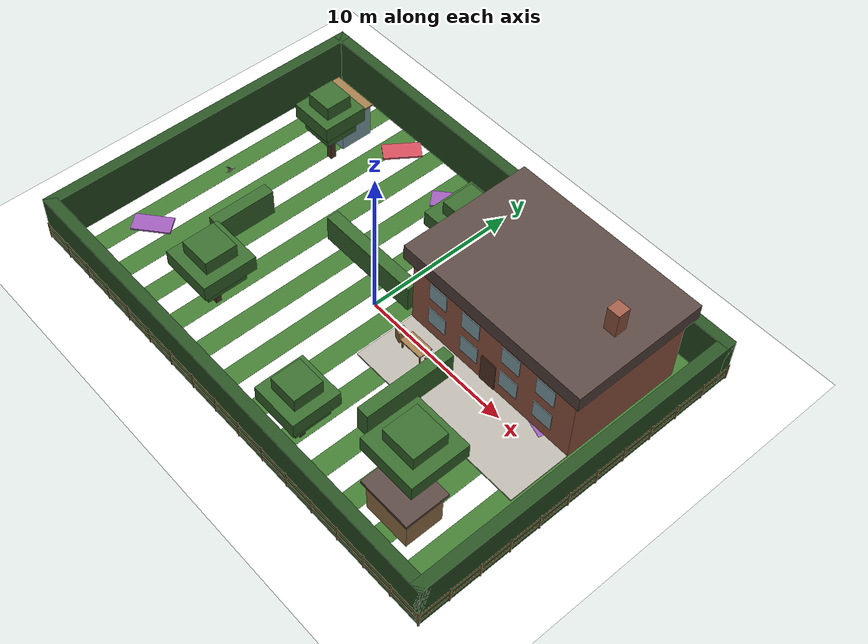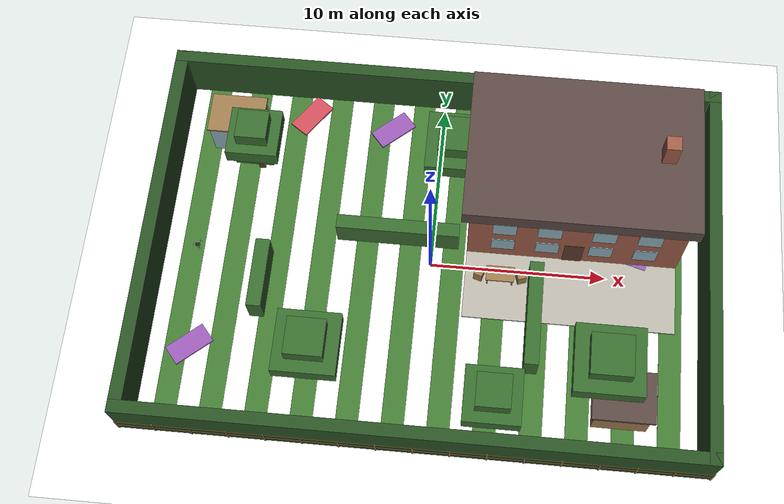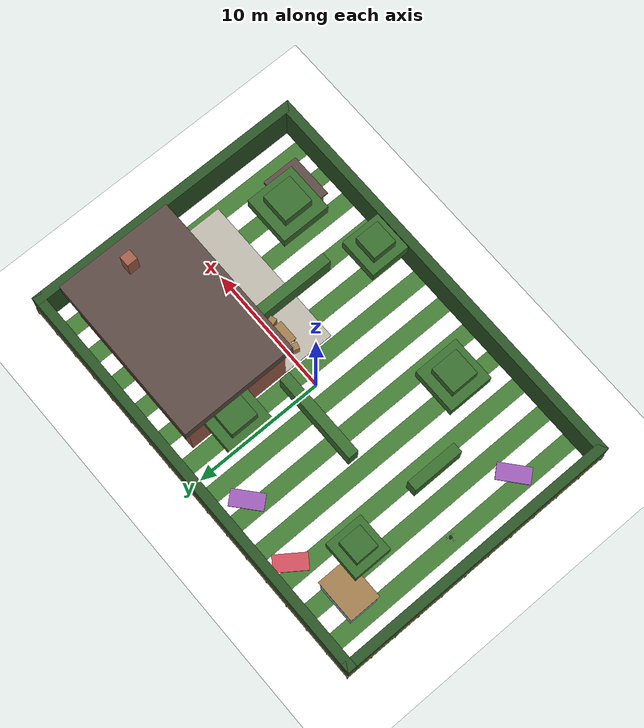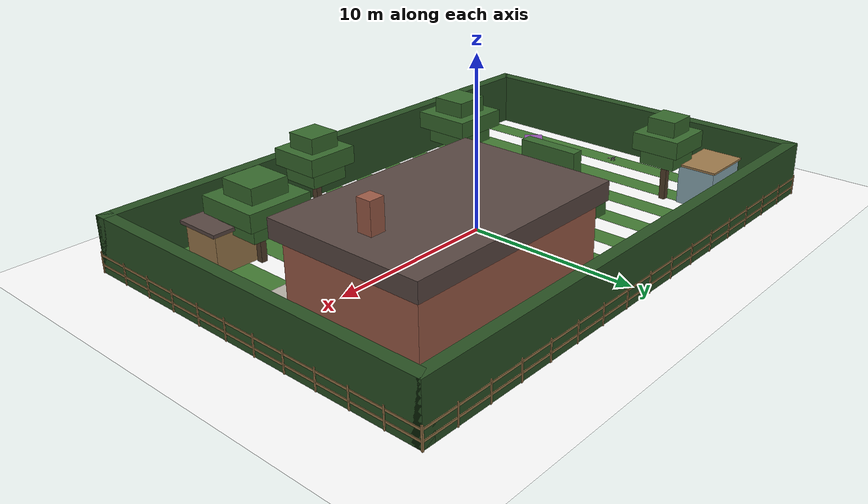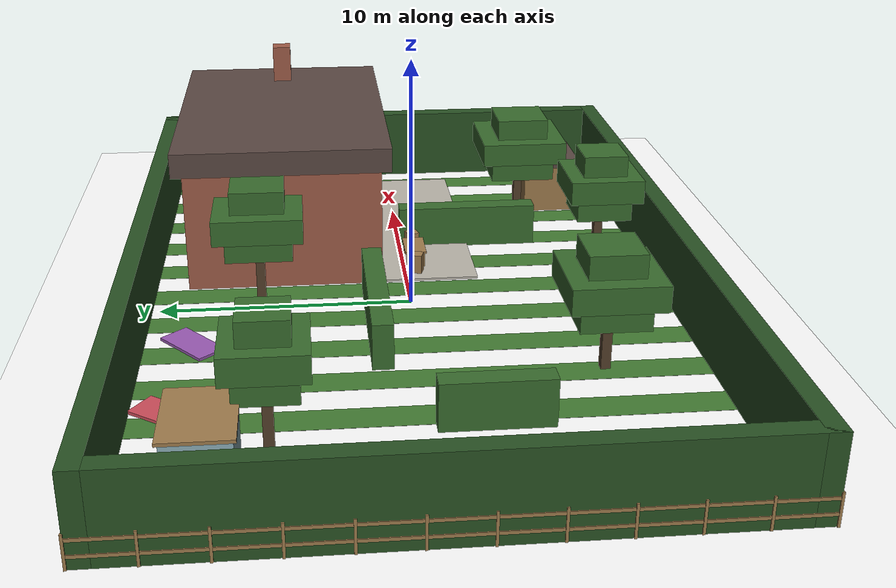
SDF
<sdf version="1.9">
 <world name="garden">
  <physics name="2ms" type="ignore">
   <max_step_size>0.002</max_step_size>
   <real_time_factor>1.0</real_time_factor>
   <dart><collision_detector>bullet</collision_detector></dart>
  </physics>
  <plugin filename="gz-sim-physics-system" name="gz::sim::systems::Physics"/>
  <plugin filename="gz-sim-user-commands-system" name="gz::sim::systems::UserCommands"/>
  <plugin filename="gz-sim-scene-broadcaster-system" name="gz::sim::systems::SceneBroadcaster"/>
  <plugin filename="gz-sim-imu-system" name="gz::sim::systems::Imu"/>
  <plugin filename="gz-sim-navsat-system" name="gz::sim::systems::NavSat"/>
  <plugin filename="gz-sim-sensors-system" name="gz::sim::systems::Sensors">
   <render_engine>ogre2</render_engine>
  </plugin>
  <gravity>0 0 -9.8066</gravity>
  <magnetic_field>2.0554e-05 0.0 4.5e-05</magnetic_field>
  <spherical_coordinates>
   <surface_model>EARTH_WGS84</surface_model>
   <world_frame_orientation>ENU</world_frame_orientation>
   <latitude_deg>49.8397</latitude_deg>
   <longitude_deg>24.0297</longitude_deg>
   <elevation>296.0</elevation>
   <heading_deg>0</heading_deg>
  </spherical_coordinates>
  <scene>
   <ambient>0.55 0.55 0.52 1</ambient>
   <background>0.55 0.68 0.85 1</background>
   <shadows>false</shadows>
   <grid>false</grid>
  </scene>
  <light name="sun" type="directional">
   <pose>0 0 12 0 0 0</pose>
   <direction>-0.4 0.3 -0.9</direction>
   <diffuse>0.9 0.88 0.82 1</diffuse>
   <specular>0.2 0.2 0.2 1</specular>
   <cast_shadows>false</cast_shadows>
  </light>
  <model name="ground_plane">
   <static>true</static>
   <link name="link">
    <collision name="collision">
     <geometry><plane><normal>0 0 1</normal><size>200 200</size></plane></geometry>
     <surface><friction><ode><mu>1.0</mu><mu2>1.0</mu2></ode></friction></surface>
    </collision>
    <visual name="visual">
     <geometry><plane><normal>0 0 1</normal><size>200 200</size></plane></geometry>
     <material>
      <ambient>0.5 0.5 0.5 1</ambient>
      <diffuse>1 1 1 1</diffuse>
      <pbr>
       <metal>
        <albedo_map>model://surfaces/materials/textures/grass.png</albedo_map>
        <metalness>0</metalness>
        <roughness>0.9</roughness>
       </metal>
      </pbr>
     </material>
    </visual>
   </link>
  </model>
  <model name="boundary">
   <static>true</static>
   <link name="link">
    <visual name="hedge_north_v">
     <pose>0 10.65 1.6 0 0 0</pose>
     <geometry><box><size>32 0.7 3.2</size></box></geometry>
     <material><ambient>0.08 0.16 0.07 1</ambient><diffuse>0.16 0.32 0.14 1</diffuse></material>
    </visual>
    <collision name="hedge_north_c">
     <pose>0 10.65 1.6 0 0 0</pose>
     <geometry><box><size>32 0.7 3.2</size></box></geometry>
    </collision>
    <visual name="hedge_south_v">
     <pose>0 -10.65 1.6 0 0 0</pose>
     <geometry><box><size>32 0.7 3.2</size></box></geometry>
     <material><ambient>0.08 0.16 0.07 1</ambient><diffuse>0.16 0.32 0.14 1</diffuse></material>
    </visual>
    <collision name="hedge_south_c">
     <pose>0 -10.65 1.6 0 0 0</pose>
     <geometry><box><size>32 0.7 3.2</size></box></geometry>
    </collision>
    <visual name="hedge_east_v">
     <pose>15.65 0 1.6 0 0 0</pose>
     <geometry><box><size>0.7 22 3.2</size></box></geometry>
     <material><ambient>0.08 0.16 0.07 1</ambient><diffuse>0.16 0.32 0.14 1</diffuse></material>
    </visual>
    <collision name="hedge_east_c">
     <pose>15.65 0 1.6 0 0 0</pose>
     <geometry><box><size>0.7 22 3.2</size></box></geometry>
    </collision>
    <visual name="hedge_west_v">
     <pose>-15.65 0 1.6 0 0 0</pose>
     <geometry><box><size>0.7 22 3.2</size></box></geometry>
     <material><ambient>0.08 0.16 0.07 1</ambient><diffuse>0.16 0.32 0.14 1</diffuse></material>
    </visual>
    <collision name="hedge_west_c">
     <pose>-15.65 0 1.6 0 0 0</pose>
     <geometry><box><size>0.7 22 3.2</size></box></geometry>
    </collision>
    <visual name="post_x0_s_v">
     <pose>-16 -11 0.6 0 0 0</pose>
     <geometry><box><size>0.09 0.09 1.2</size></box></geometry>
     <material><ambient>0.31 0.24 0.15 1</ambient><diffuse>0.62 0.48 0.3 1</diffuse></material>
    </visual>
    <collision name="post_x0_s_c">
     <pose>-16 -11 0.6 0 0 0</pose>
     <geometry><box><size>0.09 0.09 1.2</size></box></geometry>
    </collision>
    <visual name="post_x0_n_v">
     <pose>-16 11 0.6 0 0 0</pose>
     <geometry><box><size>0.09 0.09 1.2</size></box></geometry>
     <material><ambient>0.31 0.24 0.15 1</ambient><diffuse>0.62 0.48 0.3 1</diffuse></material>
    </visual>
    <collision name="post_x0_n_c">
     <pose>-16 11 0.6 0 0 0</pose>
     <geometry><box><size>0.09 0.09 1.2</size></box></geometry>
    </collision>
    <visual name="post_x1_s_v">
     <pose>-14 -11 0.6 0 0 0</pose>
     <geometry><box><size>0.09 0.09 1.2</size></box></geometry>
     <material><ambient>0.31 0.24 0.15 1</ambient><diffuse>0.62 0.48 0.3 1</diffuse></material>
    </visual>
    <collision name="post_x1_s_c">
     <pose>-14 -11 0.6 0 0 0</pose>
     <geometry><box><size>0.09 0.09 1.2</size></box></geometry>
    </collision>
    <visual name="post_x1_n_v">
     <pose>-14 11 0.6 0 0 0</pose>
     <geometry><box><size>0.09 0.09 1.2</size></box></geometry>
     <material><ambient>0.31 0.24 0.15 1</ambient><diffuse>0.62 0.48 0.3 1</diffuse></material>
    </visual>
    <collision name="post_x1_n_c">
     <pose>-14 11 0.6 0 0 0</pose>
     <geometry><box><size>0.09 0.09 1.2</size></box></geometry>
    </collision>
    <visual name="post_x2_s_v">
     <pose>-12 -11 0.6 0 0 0</pose>
     <geometry><box><size>0.09 0.09 1.2</size></box></geometry>
     <material><ambient>0.31 0.24 0.15 1</ambient><diffuse>0.62 0.48 0.3 1</diffuse></material>
    </visual>
    <collision name="post_x2_s_c">
     <pose>-12 -11 0.6 0 0 0</pose>
     <geometry><box><size>0.09 0.09 1.2</size></box></geometry>
    </collision>
    <visual name="post_x2_n_v">
     <pose>-12 11 0.6 0 0 0</pose>
     <geometry><box><size>0.09 0.09 1.2</size></box></geometry>
     <material><ambient>0.31 0.24 0.15 1</ambient><diffuse>0.62 0.48 0.3 1</diffuse></material>
    </visual>
    <collision name="post_x2_n_c">
     <pose>-12 11 0.6 0 0 0</pose>
     <geometry><box><size>0.09 0.09 1.2</size></box></geometry>
    </collision>
    <visual name="post_x3_s_v">
     <pose>-10 -11 0.6 0 0 0</pose>
     <geometry><box><size>0.09 0.09 1.2</size></box></geometry>
     <material><ambient>0.31 0.24 0.15 1</ambient><diffuse>0.62 0.48 0.3 1</diffuse></material>
    </visual>
    <collision name="post_x3_s_c">
     <pose>-10 -11 0.6 0 0 0</pose>
     <geometry><box><size>0.09 0.09 1.2</size></box></geometry>
    </collision>
    <visual name="post_x3_n_v">
     <pose>-10 11 0.6 0 0 0</pose>
     <geometry><box><size>0.09 0.09 1.2</size></box></geometry>
     <material><ambient>0.31 0.24 0.15 1</ambient><diffuse>0.62 0.48 0.3 1</diffuse></material>
    </visual>
    <collision name="post_x3_n_c">
     <pose>-10 11 0.6 0 0 0</pose>
     <geometry><box><size>0.09 0.09 1.2</size></box></geometry>
    </collision>
    <visual name="post_x4_s_v">
     <pose>-8 -11 0.6 0 0 0</pose>
     <geometry><box><size>0.09 0.09 1.2</size></box></geometry>
     <material><ambient>0.31 0.24 0.15 1</ambient><diffuse>0.62 0.48 0.3 1</diffuse></material>
    </visual>
    <collision name="post_x4_s_c">
     <pose>-8 -11 0.6 0 0 0</pose>
     <geometry><box><size>0.09 0.09 1.2</size></box></geometry>
    </collision>
    <visual name="post_x4_n_v">
     <pose>-8 11 0.6 0 0 0</pose>
     <geometry><box><size>0.09 0.09 1.2</size></box></geometry>
     <material><ambient>0.31 0.24 0.15 1</ambient><diffuse>0.62 0.48 0.3 1</diffuse></material>
    </visual>
    <collision name="post_x4_n_c">
     <pose>-8 11 0.6 0 0 0</pose>
     <geometry><box><size>0.09 0.09 1.2</size></box></geometry>
    </collision>
    <visual name="post_x5_s_v">
     <pose>-6 -11 0.6 0 0 0</pose>
     <geometry><box><size>0.09 0.09 1.2</size></box></geometry>
     <material><ambient>0.31 0.24 0.15 1</ambient><diffuse>0.62 0.48 0.3 1</diffuse></material>
    </visual>
    <collision name="post_x5_s_c">
     <pose>-6 -11 0.6 0 0 0</pose>
     <geometry><box><size>0.09 0.09 1.2</size></box></geometry>
    </collision>
    <visual name="post_x5_n_v">
     <pose>-6 11 0.6 0 0 0</pose>
     <geometry><box><size>0.09 0.09 1.2</size></box></geometry>
     <material><ambient>0.31 0.24 0.15 1</ambient><diffuse>0.62 0.48 0.3 1</diffuse></material>
    </visual>
    <collision name="post_x5_n_c">
     <pose>-6 11 0.6 0 0 0</pose>
     <geometry><box><size>0.09 0.09 1.2</size></box></geometry>
    </collision>
    <visual name="post_x6_s_v">
     <pose>-4 -11 0.6 0 0 0</pose>
     <geometry><box><size>0.09 0.09 1.2</size></box></geometry>
     <material><ambient>0.31 0.24 0.15 1</ambient><diffuse>0.62 0.48 0.3 1</diffuse></material>
    </visual>
    <collision name="post_x6_s_c">
     <pose>-4 -11 0.6 0 0 0</pose>
     <geometry><box><size>0.09 0.09 1.2</size></box></geometry>
    </collision>
    <visual name="post_x6_n_v">
     <pose>-4 11 0.6 0 0 0</pose>
     <geometry><box><size>0.09 0.09 1.2</size></box></geometry>
     <material><ambient>0.31 0.24 0.15 1</ambient><diffuse>0.62 0.48 0.3 1</diffuse></material>
    </visual>
    <collision name="post_x6_n_c">
     <pose>-4 11 0.6 0 0 0</pose>
     <geometry><box><size>0.09 0.09 1.2</size></box></geometry>
    </collision>
    <visual name="post_x7_s_v">
     <pose>-2 -11 0.6 0 0 0</pose>
     <geometry><box><size>0.09 0.09 1.2</size></box></geometry>
     <material><ambient>0.31 0.24 0.15 1</ambient><diffuse>0.62 0.48 0.3 1</diffuse></material>
    </visual>
    <collision name="post_x7_s_c">
     <pose>-2 -11 0.6 0 0 0</pose>
     <geometry><box><size>0.09 0.09 1.2</size></box></geometry>
    </collision>
    <visual name="post_x7_n_v">
     <pose>-2 11 0.6 0 0 0</pose>
     <geometry><box><size>0.09 0.09 1.2</size></box></geometry>
     <material><ambient>0.31 0.24 0.15 1</ambient><diffuse>0.62 0.48 0.3 1</diffuse></material>
    </visual>
    <collision name="post_x7_n_c">
     <pose>-2 11 0.6 0 0 0</pose>
     <geometry><box><size>0.09 0.09 1.2</size></box></geometry>
    </collision>
    <visual name="post_x8_s_v">
     <pose>0 -11 0.6 0 0 0</pose>
     <geometry><box><size>0.09 0.09 1.2</size></box></geometry>
     <material><ambient>0.31 0.24 0.15 1</ambient><diffuse>0.62 0.48 0.3 1</diffuse></material>
    </visual>
    <collision name="post_x8_s_c">
     <pose>0 -11 0.6 0 0 0</pose>
     <geometry><box><size>0.09 0.09 1.2</size></box></geometry>
    </collision>
    <visual name="post_x8_n_v">
     <pose>0 11 0.6 0 0 0</pose>
     <geometry><box><size>0.09 0.09 1.2</size></box></geometry>
     <material><ambient>0.31 0.24 0.15 1</ambient><diffuse>0.62 0.48 0.3 1</diffuse></material>
    </visual>
    <collision name="post_x8_n_c">
     <pose>0 11 0.6 0 0 0</pose>
     <geometry><box><size>0.09 0.09 1.2</size></box></geometry>
    </collision>
    <visual name="post_x9_s_v">
     <pose>2 -11 0.6 0 0 0</pose>
     <geometry><box><size>0.09 0.09 1.2</size></box></geometry>
     <material><ambient>0.31 0.24 0.15 1</ambient><diffuse>0.62 0.48 0.3 1</diffuse></material>
    </visual>
    <collision name="post_x9_s_c">
     <pose>2 -11 0.6 0 0 0</pose>
     <geometry><box><size>0.09 0.09 1.2</size></box></geometry>
    </collision>
    <visual name="post_x9_n_v">
     <pose>2 11 0.6 0 0 0</pose>
     <geometry><box><size>0.09 0.09 1.2</size></box></geometry>
     <material><ambient>0.31 0.24 0.15 1</ambient><diffuse>0.62 0.48 0.3 1</diffuse></material>
    </visual>
    <collision name="post_x9_n_c">
     <pose>2 11 0.6 0 0 0</pose>
     <geometry><box><size>0.09 0.09 1.2</size></box></geometry>
    </collision>
    <visual name="post_x10_s_v">
     <pose>4 -11 0.6 0 0 0</pose>
     <geometry><box><size>0.09 0.09 1.2</size></box></geometry>
     <material><ambient>0.31 0.24 0.15 1</ambient><diffuse>0.62 0.48 0.3 1</diffuse></material>
    </visual>
    <collision name="post_x10_s_c">
     <pose>4 -11 0.6 0 0 0</pose>
     <geometry><box><size>0.09 0.09 1.2</size></box></geometry>
    </collision>
    <visual name="post_x10_n_v">
     <pose>4 11 0.6 0 0 0</pose>
     <geometry><box><size>0.09 0.09 1.2</size></box></geometry>
     <material><ambient>0.31 0.24 0.15 1</ambient><diffuse>0.62 0.48 0.3 1</diffuse></material>
    </visual>
    <collision name="post_x10_n_c">
     <pose>4 11 0.6 0 0 0</pose>
     <geometry><box><size>0.09 0.09 1.2</size></box></geometry>
    </collision>
    <visual name="post_x11_s_v">
     <pose>6 -11 0.6 0 0 0</pose>
     <geometry><box><size>0.09 0.09 1.2</size></box></geometry>
     <material><ambient>0.31 0.24 0.15 1</ambient><diffuse>0.62 0.48 0.3 1</diffuse></material>
    </visual>
    <collision name="post_x11_s_c">
     <pose>6 -11 0.6 0 0 0</pose>
     <geometry><box><size>0.09 0.09 1.2</size></box></geometry>
    </collision>
    <visual name="post_x11_n_v">
     <pose>6 11 0.6 0 0 0</pose>
     <geometry><box><size>0.09 0.09 1.2</size></box></geometry>
     <material><ambient>0.31 0.24 0.15 1</ambient><diffuse>0.62 0.48 0.3 1</diffuse></material>
    </visual>
    <collision name="post_x11_n_c">
     <pose>6 11 0.6 0 0 0</pose>
     <geometry><box><size>0.09 0.09 1.2</size></box></geometry>
    </collision>
    <visual name="post_x12_s_v">
     <pose>8 -11 0.6 0 0 0</pose>
     <geometry><box><size>0.09 0.09 1.2</size></box></geometry>
     <material><ambient>0.31 0.24 0.15 1</ambient><diffuse>0.62 0.48 0.3 1</diffuse></material>
    </visual>
    <collision name="post_x12_s_c">
     <pose>8 -11 0.6 0 0 0</pose>
     <geometry><box><size>0.09 0.09 1.2</size></box></geometry>
    </collision>
    <visual name="post_x12_n_v">
     <pose>8 11 0.6 0 0 0</pose>
     <geometry><box><size>0.09 0.09 1.2</size></box></geometry>
     <material><ambient>0.31 0.24 0.15 1</ambient><diffuse>0.62 0.48 0.3 1</diffuse></material>
    </visual>
    <collision name="post_x12_n_c">
     <pose>8 11 0.6 0 0 0</pose>
     <geometry><box><size>0.09 0.09 1.2</size></box></geometry>
    </collision>
    <visual name="post_x13_s_v">
     <pose>10 -11 0.6 0 0 0</pose>
     <geometry><box><size>0.09 0.09 1.2</size></box></geometry>
     <material><ambient>0.31 0.24 0.15 1</ambient><diffuse>0.62 0.48 0.3 1</diffuse></material>
    </visual>
    <collision name="post_x13_s_c">
     <pose>10 -11 0.6 0 0 0</pose>
     <geometry><box><size>0.09 0.09 1.2</size></box></geometry>
    </collision>
    <visual name="post_x13_n_v">
     <pose>10 11 0.6 0 0 0</pose>
     <geometry><box><size>0.09 0.09 1.2</size></box></geometry>
     <material><ambient>0.31 0.24 0.15 1</ambient><diffuse>0.62 0.48 0.3 1</diffuse></material>
    </visual>
    <collision name="post_x13_n_c">
     <pose>10 11 0.6 0 0 0</pose>
     <geometry><box><size>0.09 0.09 1.2</size></box></geometry>
    </collision>
    <visual name="post_x14_s_v">
     <pose>12 -11 0.6 0 0 0</pose>
     <geometry><box><size>0.09 0.09 1.2</size></box></geometry>
     <material><ambient>0.31 0.24 0.15 1</ambient><diffuse>0.62 0.48 0.3 1</diffuse></material>
    </visual>
    <collision name="post_x14_s_c">
     <pose>12 -11 0.6 0 0 0</pose>
     <geometry><box><size>0.09 0.09 1.2</size></box></geometry>
    </collision>
    <visual name="post_x14_n_v">
     <pose>12 11 0.6 0 0 0</pose>
     <geometry><box><size>0.09 0.09 1.2</size></box></geometry>
     <material><ambient>0.31 0.24 0.15 1</ambient><diffuse>0.62 0.48 0.3 1</diffuse></material>
    </visual>
    <collision name="post_x14_n_c">
     <pose>12 11 0.6 0 0 0</pose>
     <geometry><box><size>0.09 0.09 1.2</size></box></geometry>
    </collision>
    <visual name="post_x15_s_v">
     <pose>14 -11 0.6 0 0 0</pose>
     <geometry><box><size>0.09 0.09 1.2</size></box></geometry>
     <material><ambient>0.31 0.24 0.15 1</ambient><diffuse>0.62 0.48 0.3 1</diffuse></material>
    </visual>
    <collision name="post_x15_s_c">
     <pose>14 -11 0.6 0 0 0</pose>
     <geometry><box><size>0.09 0.09 1.2</size></box></geometry>
    </collision>
    <visual name="post_x15_n_v">
     <pose>14 11 0.6 0 0 0</pose>
     <geometry><box><size>0.09 0.09 1.2</size></box></geometry>
     <material><ambient>0.31 0.24 0.15 1</ambient><diffuse>0.62 0.48 0.3 1</diffuse></material>
    </visual>
    <collision name="post_x15_n_c">
     <pose>14 11 0.6 0 0 0</pose>
     <geometry><box><size>0.09 0.09 1.2</size></box></geometry>
    </collision>
    <visual name="post_x16_s_v">
     <pose>16 -11 0.6 0 0 0</pose>
     <geometry><box><size>0.09 0.09 1.2</size></box></geometry>
     <material><ambient>0.31 0.24 0.15 1</ambient><diffuse>0.62 0.48 0.3 1</diffuse></material>
    </visual>
    <collision name="post_x16_s_c">
     <pose>16 -11 0.6 0 0 0</pose>
     <geometry><box><size>0.09 0.09 1.2</size></box></geometry>
    </collision>
    <visual name="post_x16_n_v">
     <pose>16 11 0.6 0 0 0</pose>
     <geometry><box><size>0.09 0.09 1.2</size></box></geometry>
     <material><ambient>0.31 0.24 0.15 1</ambient><diffuse>0.62 0.48 0.3 1</diffuse></material>
    </visual>
    <collision name="post_x16_n_c">
     <pose>16 11 0.6 0 0 0</pose>
     <geometry><box><size>0.09 0.09 1.2</size></box></geometry>
    </collision>
    <visual name="post_y0_w_v">
     <pose>-16 -11 0.6 0 0 0</pose>
     <geometry><box><size>0.09 0.09 1.2</size></box></geometry>
     <material><ambient>0.31 0.24 0.15 1</ambient><diffuse>0.62 0.48 0.3 1</diffuse></material>
    </visual>
    <collision name="post_y0_w_c">
     <pose>-16 -11 0.6 0 0 0</pose>
     <geometry><box><size>0.09 0.09 1.2</size></box></geometry>
    </collision>
    <visual name="post_y0_e_v">
     <pose>16 -11 0.6 0 0 0</pose>
     <geometry><box><size>0.09 0.09 1.2</size></box></geometry>
     <material><ambient>0.31 0.24 0.15 1</ambient><diffuse>0.62 0.48 0.3 1</diffuse></material>
    </visual>
    <collision name="post_y0_e_c">
     <pose>16 -11 0.6 0 0 0</pose>
     <geometry><box><size>0.09 0.09 1.2</size></box></geometry>
    </collision>
    <visual name="post_y1_w_v">
     <pose>-16 -9 0.6 0 0 0</pose>
     <geometry><box><size>0.09 0.09 1.2</size></box></geometry>
     <material><ambient>0.31 0.24 0.15 1</ambient><diffuse>0.62 0.48 0.3 1</diffuse></material>
    </visual>
    <collision name="post_y1_w_c">
     <pose>-16 -9 0.6 0 0 0</pose>
     <geometry><box><size>0.09 0.09 1.2</size></box></geometry>
    </collision>
    <visual name="post_y1_e_v">
     <pose>16 -9 0.6 0 0 0</pose>
     <geometry><box><size>0.09 0.09 1.2</size></box></geometry>
     <material><ambient>0.31 0.24 0.15 1</ambient><diffuse>0.62 0.48 0.3 1</diffuse></material>
    </visual>
    <collision name="post_y1_e_c">
     <pose>16 -9 0.6 0 0 0</pose>
     <geometry><box><size>0.09 0.09 1.2</size></box></geometry>
    </collision>
    <visual name="post_y2_w_v">
     <pose>-16 -7 0.6 0 0 0</pose>
     <geometry><box><size>0.09 0.09 1.2</size></box></geometry>
     <material><ambient>0.31 0.24 0.15 1</ambient><diffuse>0.62 0.48 0.3 1</diffuse></material>
    </visual>
    <collision name="post_y2_w_c">
     <pose>-16 -7 0.6 0 0 0</pose>
     <geometry><box><size>0.09 0.09 1.2</size></box></geometry>
    </collision>
    <visual name="post_y2_e_v">
     <pose>16 -7 0.6 0 0 0</pose>
     <geometry><box><size>0.09 0.09 1.2</size></box></geometry>
     <material><ambient>0.31 0.24 0.15 1</ambient><diffuse>0.62 0.48 0.3 1</diffuse></material>
    </visual>
    <collision name="post_y2_e_c">
     <pose>16 -7 0.6 0 0 0</pose>
     <geometry><box><size>0.09 0.09 1.2</size></box></geometry>
    </collision>
    <visual name="post_y3_w_v">
     <pose>-16 -5 0.6 0 0 0</pose>
     <geometry><box><size>0.09 0.09 1.2</size></box></geometry>
     <material><ambient>0.31 0.24 0.15 1</ambient><diffuse>0.62 0.48 0.3 1</diffuse></material>
    </visual>
    <collision name="post_y3_w_c">
     <pose>-16 -5 0.6 0 0 0</pose>
     <geometry><box><size>0.09 0.09 1.2</size></box></geometry>
    </collision>
    <visual name="post_y3_e_v">
     <pose>16 -5 0.6 0 0 0</pose>
     <geometry><box><size>0.09 0.09 1.2</size></box></geometry>
     <material><ambient>0.31 0.24 0.15 1</ambient><diffuse>0.62 0.48 0.3 1</diffuse></material>
    </visual>
    <collision name="post_y3_e_c">
     <pose>16 -5 0.6 0 0 0</pose>
     <geometry><box><size>0.09 0.09 1.2</size></box></geometry>
    </collision>
    <visual name="post_y4_w_v">
     <pose>-16 -3 0.6 0 0 0</pose>
     <geometry><box><size>0.09 0.09 1.2</size></box></geometry>
     <material><ambient>0.31 0.24 0.15 1</ambient><diffuse>0.62 0.48 0.3 1</diffuse></material>
    </visual>
    <collision name="post_y4_w_c">
     <pose>-16 -3 0.6 0 0 0</pose>
     <geometry><box><size>0.09 0.09 1.2</size></box></geometry>
    </collision>
    <visual name="post_y4_e_v">
     <pose>16 -3 0.6 0 0 0</pose>
     <geometry><box><size>0.09 0.09 1.2</size></box></geometry>
     <material><ambient>0.31 0.24 0.15 1</ambient><diffuse>0.62 0.48 0.3 1</diffuse></material>
    </visual>
    <collision name="post_y4_e_c">
     <pose>16 -3 0.6 0 0 0</pose>
     <geometry><box><size>0.09 0.09 1.2</size></box></geometry>
    </collision>
    <visual name="post_y5_w_v">
     <pose>-16 -1 0.6 0 0 0</pose>
     <geometry><box><size>0.09 0.09 1.2</size></box></geometry>
     <material><ambient>0.31 0.24 0.15 1</ambient><diffuse>0.62 0.48 0.3 1</diffuse></material>
    </visual>
    <collision name="post_y5_w_c">
     <pose>-16 -1 0.6 0 0 0</pose>
     <geometry><box><size>0.09 0.09 1.2</size></box></geometry>
    </collision>
    <visual name="post_y5_e_v">
     <pose>16 -1 0.6 0 0 0</pose>
     <geometry><box><size>0.09 0.09 1.2</size></box></geometry>
     <material><ambient>0.31 0.24 0.15 1</ambient><diffuse>0.62 0.48 0.3 1</diffuse></material>
    </visual>
    <collision name="post_y5_e_c">
     <pose>16 -1 0.6 0 0 0</pose>
     <geometry><box><size>0.09 0.09 1.2</size></box></geometry>
    </collision>
    <visual name="post_y6_w_v">
     <pose>-16 1 0.6 0 0 0</pose>
     <geometry><box><size>0.09 0.09 1.2</size></box></geometry>
     <material><ambient>0.31 0.24 0.15 1</ambient><diffuse>0.62 0.48 0.3 1</diffuse></material>
    </visual>
    <collision name="post_y6_w_c">
     <pose>-16 1 0.6 0 0 0</pose>
     <geometry><box><size>0.09 0.09 1.2</size></box></geometry>
    </collision>
    <visual name="post_y6_e_v">
     <pose>16 1 0.6 0 0 0</pose>
     <geometry><box><size>0.09 0.09 1.2</size></box></geometry>
     <material><ambient>0.31 0.24 0.15 1</ambient><diffuse>0.62 0.48 0.3 1</diffuse></material>
    </visual>
    <collision name="post_y6_e_c">
     <pose>16 1 0.6 0 0 0</pose>
     <geometry><box><size>0.09 0.09 1.2</size></box></geometry>
    </collision>
    <visual name="post_y7_w_v">
     <pose>-16 3 0.6 0 0 0</pose>
     <geometry><box><size>0.09 0.09 1.2</size></box></geometry>
     <material><ambient>0.31 0.24 0.15 1</ambient><diffuse>0.62 0.48 0.3 1</diffuse></material>
    </visual>
    <collision name="post_y7_w_c">
     <pose>-16 3 0.6 0 0 0</pose>
     <geometry><box><size>0.09 0.09 1.2</size></box></geometry>
    </collision>
    <visual name="post_y7_e_v">
     <pose>16 3 0.6 0 0 0</pose>
     <geometry><box><size>0.09 0.09 1.2</size></box></geometry>
     <material><ambient>0.31 0.24 0.15 1</ambient><diffuse>0.62 0.48 0.3 1</diffuse></material>
    </visual>
    <collision name="post_y7_e_c">
     <pose>16 3 0.6 0 0 0</pose>
     <geometry><box><size>0.09 0.09 1.2</size></box></geometry>
    </collision>
    <visual name="post_y8_w_v">
     <pose>-16 5 0.6 0 0 0</pose>
     <geometry><box><size>0.09 0.09 1.2</size></box></geometry>
     <material><ambient>0.31 0.24 0.15 1</ambient><diffuse>0.62 0.48 0.3 1</diffuse></material>
    </visual>
    <collision name="post_y8_w_c">
     <pose>-16 5 0.6 0 0 0</pose>
     <geometry><box><size>0.09 0.09 1.2</size></box></geometry>
    </collision>
    <visual name="post_y8_e_v">
     <pose>16 5 0.6 0 0 0</pose>
     <geometry><box><size>0.09 0.09 1.2</size></box></geometry>
     <material><ambient>0.31 0.24 0.15 1</ambient><diffuse>0.62 0.48 0.3 1</diffuse></material>
    </visual>
    <collision name="post_y8_e_c">
     <pose>16 5 0.6 0 0 0</pose>
     <geometry><box><size>0.09 0.09 1.2</size></box></geometry>
    </collision>
    <visual name="post_y9_w_v">
     <pose>-16 7 0.6 0 0 0</pose>
     <geometry><box><size>0.09 0.09 1.2</size></box></geometry>
     <material><ambient>0.31 0.24 0.15 1</ambient><diffuse>0.62 0.48 0.3 1</diffuse></material>
    </visual>
    <collision name="post_y9_w_c">
     <pose>-16 7 0.6 0 0 0</pose>
     <geometry><box><size>0.09 0.09 1.2</size></box></geometry>
    </collision>
    <visual name="post_y9_e_v">
     <pose>16 7 0.6 0 0 0</pose>
     <geometry><box><size>0.09 0.09 1.2</size></box></geometry>
     <material><ambient>0.31 0.24 0.15 1</ambient><diffuse>0.62 0.48 0.3 1</diffuse></material>
    </visual>
    <collision name="post_y9_e_c">
     <pose>16 7 0.6 0 0 0</pose>
     <geometry><box><size>0.09 0.09 1.2</size></box></geometry>
    </collision>
    <visual name="post_y10_w_v">
     <pose>-16 9 0.6 0 0 0</pose>
     <geometry><box><size>0.09 0.09 1.2</size></box></geometry>
     <material><ambient>0.31 0.24 0.15 1</ambient><diffuse>0.62 0.48 0.3 1</diffuse></material>
    </visual>
    <collision name="post_y10_w_c">
     <pose>-16 9 0.6 0 0 0</pose>
     <geometry><box><size>0.09 0.09 1.2</size></box></geometry>
    </collision>
    <visual name="post_y10_e_v">
     <pose>16 9 0.6 0 0 0</pose>
     <geometry><box><size>0.09 0.09 1.2</size></box></geometry>
     <material><ambient>0.31 0.24 0.15 1</ambient><diffuse>0.62 0.48 0.3 1</diffuse></material>
    </visual>
    <collision name="post_y10_e_c">
     <pose>16 9 0.6 0 0 0</pose>
     <geometry><box><size>0.09 0.09 1.2</size></box></geometry>
    </collision>
    <visual name="post_y11_w_v">
     <pose>-16 11 0.6 0 0 0</pose>
     <geometry><box><size>0.09 0.09 1.2</size></box></geometry>
     <material><ambient>0.31 0.24 0.15 1</ambient><diffuse>0.62 0.48 0.3 1</diffuse></material>
    </visual>
    <collision name="post_y11_w_c">
     <pose>-16 11 0.6 0 0 0</pose>
     <geometry><box><size>0.09 0.09 1.2</size></box></geometry>
    </collision>
    <visual name="post_y11_e_v">
     <pose>16 11 0.6 0 0 0</pose>
     <geometry><box><size>0.09 0.09 1.2</size></box></geometry>
     <material><ambient>0.31 0.24 0.15 1</ambient><diffuse>0.62 0.48 0.3 1</diffuse></material>
    </visual>
    <collision name="post_y11_e_c">
     <pose>16 11 0.6 0 0 0</pose>
     <geometry><box><size>0.09 0.09 1.2</size></box></geometry>
    </collision>
    <visual name="rail_x0_s_v">
     <pose>0 -11 0.45 0 0 0</pose>
     <geometry><box><size>32 0.06 0.12</size></box></geometry>
     <material><ambient>0.31 0.24 0.15 1</ambient><diffuse>0.62 0.48 0.3 1</diffuse></material>
    </visual>
    <visual name="rail_x0_n_v">
     <pose>0 11 0.45 0 0 0</pose>
     <geometry><box><size>32 0.06 0.12</size></box></geometry>
     <material><ambient>0.31 0.24 0.15 1</ambient><diffuse>0.62 0.48 0.3 1</diffuse></material>
    </visual>
    <visual name="rail_y0_w_v">
     <pose>-16 0 0.45 0 0 0</pose>
     <geometry><box><size>0.06 22 0.12</size></box></geometry>
     <material><ambient>0.31 0.24 0.15 1</ambient><diffuse>0.62 0.48 0.3 1</diffuse></material>
    </visual>
    <visual name="rail_y0_e_v">
     <pose>16 0 0.45 0 0 0</pose>
     <geometry><box><size>0.06 22 0.12</size></box></geometry>
     <material><ambient>0.31 0.24 0.15 1</ambient><diffuse>0.62 0.48 0.3 1</diffuse></material>
    </visual>
    <visual name="rail_x1_s_v">
     <pose>0 -11 1 0 0 0</pose>
     <geometry><box><size>32 0.06 0.12</size></box></geometry>
     <material><ambient>0.31 0.24 0.15 1</ambient><diffuse>0.62 0.48 0.3 1</diffuse></material>
    </visual>
    <visual name="rail_x1_n_v">
     <pose>0 11 1 0 0 0</pose>
     <geometry><box><size>32 0.06 0.12</size></box></geometry>
     <material><ambient>0.31 0.24 0.15 1</ambient><diffuse>0.62 0.48 0.3 1</diffuse></material>
    </visual>
    <visual name="rail_y1_w_v">
     <pose>-16 0 1 0 0 0</pose>
     <geometry><box><size>0.06 22 0.12</size></box></geometry>
     <material><ambient>0.31 0.24 0.15 1</ambient><diffuse>0.62 0.48 0.3 1</diffuse></material>
    </visual>
    <visual name="rail_y1_e_v">
     <pose>16 0 1 0 0 0</pose>
     <geometry><box><size>0.06 22 0.12</size></box></geometry>
     <material><ambient>0.31 0.24 0.15 1</ambient><diffuse>0.62 0.48 0.3 1</diffuse></material>
    </visual>
   </link>
  </model>
  <model name="house">
   <static>true</static>
   <pose>8 5 0 0 0 0</pose>
   <link name="link">
    <visual name="walls_v">
     <pose>0 0 2.5 0 0 0</pose>
     <geometry><box><size>12 8 5</size></box></geometry>
     <material><ambient>0.31 0.18 0.14 1</ambient><diffuse>0.62 0.36 0.28 1</diffuse></material>
    </visual>
    <collision name="walls_c">
     <pose>0 0 2.5 0 0 0</pose>
     <geometry><box><size>12 8 5</size></box></geometry>
    </collision>
    <visual name="roof_v">
     <pose>0 0 5.5 0 0 0</pose>
     <geometry><box><size>12.8 8.8 1</size></box></geometry>
     <material><ambient>0.175 0.14 0.13 1</ambient><diffuse>0.35 0.28 0.26 1</diffuse></material>
    </visual>
    <collision name="roof_c">
     <pose>0 0 5.5 0 0 0</pose>
     <geometry><box><size>12.8 8.8 1</size></box></geometry>
    </collision>
    <visual name="chimney_v">
     <pose>4.5 0 6.8 0 0 0</pose>
     <geometry><box><size>0.8 0.8 1.6</size></box></geometry>
     <material><ambient>0.31 0.18 0.14 1</ambient><diffuse>0.62 0.36 0.28 1</diffuse></material>
    </visual>
    <collision name="chimney_c">
     <pose>4.5 0 6.8 0 0 0</pose>
     <geometry><box><size>0.8 0.8 1.6</size></box></geometry>
    </collision>
    <visual name="window_0_0_v">
     <pose>-4 -4.02 1.6 0 0 0</pose>
     <geometry><box><size>1.3 0.06 1.2</size></box></geometry>
     <material><ambient>0.275 0.34 0.36 1</ambient><diffuse>0.55 0.68 0.72 1</diffuse></material>
    </visual>
    <visual name="window_0_1_v">
     <pose>-4 -4.02 3.6 0 0 0</pose>
     <geometry><box><size>1.3 0.06 1.2</size></box></geometry>
     <material><ambient>0.275 0.34 0.36 1</ambient><diffuse>0.55 0.68 0.72 1</diffuse></material>
    </visual>
    <visual name="window_1_0_v">
     <pose>-1.5 -4.02 1.6 0 0 0</pose>
     <geometry><box><size>1.3 0.06 1.2</size></box></geometry>
     <material><ambient>0.275 0.34 0.36 1</ambient><diffuse>0.55 0.68 0.72 1</diffuse></material>
    </visual>
    <visual name="window_1_1_v">
     <pose>-1.5 -4.02 3.6 0 0 0</pose>
     <geometry><box><size>1.3 0.06 1.2</size></box></geometry>
     <material><ambient>0.275 0.34 0.36 1</ambient><diffuse>0.55 0.68 0.72 1</diffuse></material>
    </visual>
    <visual name="window_2_0_v">
     <pose>1.5 -4.02 1.6 0 0 0</pose>
     <geometry><box><size>1.3 0.06 1.2</size></box></geometry>
     <material><ambient>0.275 0.34 0.36 1</ambient><diffuse>0.55 0.68 0.72 1</diffuse></material>
    </visual>
    <visual name="window_2_1_v">
     <pose>1.5 -4.02 3.6 0 0 0</pose>
     <geometry><box><size>1.3 0.06 1.2</size></box></geometry>
     <material><ambient>0.275 0.34 0.36 1</ambient><diffuse>0.55 0.68 0.72 1</diffuse></material>
    </visual>
    <visual name="window_3_0_v">
     <pose>4 -4.02 1.6 0 0 0</pose>
     <geometry><box><size>1.3 0.06 1.2</size></box></geometry>
     <material><ambient>0.275 0.34 0.36 1</ambient><diffuse>0.55 0.68 0.72 1</diffuse></material>
    </visual>
    <visual name="window_3_1_v">
     <pose>4 -4.02 3.6 0 0 0</pose>
     <geometry><box><size>1.3 0.06 1.2</size></box></geometry>
     <material><ambient>0.275 0.34 0.36 1</ambient><diffuse>0.55 0.68 0.72 1</diffuse></material>
    </visual>
    <visual name="door_v">
     <pose>0 -4.02 1.05 0 0 0</pose>
     <geometry><box><size>1.1 0.06 2.1</size></box></geometry>
     <material><ambient>0.175 0.11 0.08 1</ambient><diffuse>0.35 0.22 0.16 1</diffuse></material>
    </visual>
    <visual name="terrace_v">
     <pose>0 -6 0.05 0 0 0</pose>
     <geometry><box><size>12 4 0.1</size></box></geometry>
     <material><ambient>0.36 0.35 0.33 1</ambient><diffuse>0.72 0.7 0.66 1</diffuse></material>
    </visual>
    <collision name="terrace_c">
     <pose>0 -6 0.05 0 0 0</pose>
     <geometry><box><size>12 4 0.1</size></box></geometry>
    </collision>
   </link>
  </model>
  <model name="tree_0">
   <static>true</static>
   <pose>-6 -6.5 0 0 0 0</pose>
   <link name="link">
    <visual name="trunk_v">
     <pose>0 0 1.071 0 0 0</pose>
     <geometry><box><size>0.36 0.36 2.143</size></box></geometry>
     <material><ambient>0.16 0.12 0.08 1</ambient><diffuse>0.32 0.24 0.16 1</diffuse></material>
    </visual>
    <collision name="trunk_c">
     <pose>0 0 1.071 0 0 0</pose>
     <geometry><box><size>0.36 0.36 2.143</size></box></geometry>
    </collision>
    <visual name="canopy_0_v">
     <pose>0 0 2.543 0 0 0</pose>
     <geometry><box><size>2.59 2.59 1</size></box></geometry>
     <material><ambient>0.11 0.21 0.09 1</ambient><diffuse>0.22 0.42 0.18 1</diffuse></material>
    </visual>
    <collision name="canopy_0_c">
     <pose>0 0 2.543 0 0 0</pose>
     <geometry><box><size>2.59 2.59 1</size></box></geometry>
    </collision>
    <visual name="canopy_1_v">
     <pose>0 0 3.443 0 0 0</pose>
     <geometry><box><size>3.453 3.453 1</size></box></geometry>
     <material><ambient>0.11 0.21 0.09 1</ambient><diffuse>0.22 0.42 0.18 1</diffuse></material>
    </visual>
    <collision name="canopy_1_c">
     <pose>0 0 3.443 0 0 0</pose>
     <geometry><box><size>3.453 3.453 1</size></box></geometry>
    </collision>
    <visual name="canopy_2_v">
     <pose>0 0 4.343 0 0 0</pose>
     <geometry><box><size>2.072 2.072 1</size></box></geometry>
     <material><ambient>0.11 0.21 0.09 1</ambient><diffuse>0.22 0.42 0.18 1</diffuse></material>
    </visual>
    <collision name="canopy_2_c">
     <pose>0 0 4.343 0 0 0</pose>
     <geometry><box><size>2.072 2.072 1</size></box></geometry>
    </collision>
   </link>
  </model>
  <model name="tree_1">
   <static>true</static>
   <pose>1 6 0 0 0 0</pose>
   <link name="link">
    <visual name="trunk_v">
     <pose>0 0 1.111 0 0 0</pose>
     <geometry><box><size>0.36 0.36 2.222</size></box></geometry>
     <material><ambient>0.16 0.12 0.08 1</ambient><diffuse>0.32 0.24 0.16 1</diffuse></material>
    </visual>
    <collision name="trunk_c">
     <pose>0 0 1.111 0 0 0</pose>
     <geometry><box><size>0.36 0.36 2.222</size></box></geometry>
    </collision>
    <visual name="canopy_0_v">
     <pose>0 0 2.622 0 0 0</pose>
     <geometry><box><size>2.644 2.644 1</size></box></geometry>
     <material><ambient>0.11 0.21 0.09 1</ambient><diffuse>0.22 0.42 0.18 1</diffuse></material>
    </visual>
    <collision name="canopy_0_c">
     <pose>0 0 2.622 0 0 0</pose>
     <geometry><box><size>2.644 2.644 1</size></box></geometry>
    </collision>
    <visual name="canopy_1_v">
     <pose>0 0 3.522 0 0 0</pose>
     <geometry><box><size>3.525 3.525 1</size></box></geometry>
     <material><ambient>0.11 0.21 0.09 1</ambient><diffuse>0.22 0.42 0.18 1</diffuse></material>
    </visual>
    <collision name="canopy_1_c">
     <pose>0 0 3.522 0 0 0</pose>
     <geometry><box><size>3.525 3.525 1</size></box></geometry>
    </collision>
    <visual name="canopy_2_v">
     <pose>0 0 4.422 0 0 0</pose>
     <geometry><box><size>2.115 2.115 1</size></box></geometry>
     <material><ambient>0.11 0.21 0.09 1</ambient><diffuse>0.22 0.42 0.18 1</diffuse></material>
    </visual>
    <collision name="canopy_2_c">
     <pose>0 0 4.422 0 0 0</pose>
     <geometry><box><size>2.115 2.115 1</size></box></geometry>
    </collision>
   </link>
  </model>
  <model name="tree_2">
   <static>true</static>
   <pose>-10.5 5.5 0 0 0 0</pose>
   <link name="link">
    <visual name="trunk_v">
     <pose>0 0 1.188 0 0 0</pose>
     <geometry><box><size>0.36 0.36 2.375</size></box></geometry>
     <material><ambient>0.16 0.12 0.08 1</ambient><diffuse>0.32 0.24 0.16 1</diffuse></material>
    </visual>
    <collision name="trunk_c">
     <pose>0 0 1.188 0 0 0</pose>
     <geometry><box><size>0.36 0.36 2.375</size></box></geometry>
    </collision>
    <visual name="canopy_0_v">
     <pose>0 0 2.775 0 0 0</pose>
     <geometry><box><size>2.159 2.159 1</size></box></geometry>
     <material><ambient>0.11 0.21 0.09 1</ambient><diffuse>0.22 0.42 0.18 1</diffuse></material>
    </visual>
    <collision name="canopy_0_c">
     <pose>0 0 2.775 0 0 0</pose>
     <geometry><box><size>2.159 2.159 1</size></box></geometry>
    </collision>
    <visual name="canopy_1_v">
     <pose>0 0 3.675 0 0 0</pose>
     <geometry><box><size>2.879 2.879 1</size></box></geometry>
     <material><ambient>0.11 0.21 0.09 1</ambient><diffuse>0.22 0.42 0.18 1</diffuse></material>
    </visual>
    <collision name="canopy_1_c">
     <pose>0 0 3.675 0 0 0</pose>
     <geometry><box><size>2.879 2.879 1</size></box></geometry>
    </collision>
    <visual name="canopy_2_v">
     <pose>0 0 4.575 0 0 0</pose>
     <geometry><box><size>1.727 1.727 1</size></box></geometry>
     <material><ambient>0.11 0.21 0.09 1</ambient><diffuse>0.22 0.42 0.18 1</diffuse></material>
    </visual>
    <collision name="canopy_2_c">
     <pose>0 0 4.575 0 0 0</pose>
     <geometry><box><size>1.727 1.727 1</size></box></geometry>
    </collision>
   </link>
  </model>
  <model name="tree_3">
   <static>true</static>
   <pose>10 -6 0 0 0 0</pose>
   <link name="link">
    <visual name="trunk_v">
     <pose>0 0 1.004 0 0 0</pose>
     <geometry><box><size>0.36 0.36 2.008</size></box></geometry>
     <material><ambient>0.16 0.12 0.08 1</ambient><diffuse>0.32 0.24 0.16 1</diffuse></material>
    </visual>
    <collision name="trunk_c">
     <pose>0 0 1.004 0 0 0</pose>
     <geometry><box><size>0.36 0.36 2.008</size></box></geometry>
    </collision>
    <visual name="canopy_0_v">
     <pose>0 0 2.408 0 0 0</pose>
     <geometry><box><size>2.854 2.854 1</size></box></geometry>
     <material><ambient>0.11 0.21 0.09 1</ambient><diffuse>0.22 0.42 0.18 1</diffuse></material>
    </visual>
    <collision name="canopy_0_c">
     <pose>0 0 2.408 0 0 0</pose>
     <geometry><box><size>2.854 2.854 1</size></box></geometry>
    </collision>
    <visual name="canopy_1_v">
     <pose>0 0 3.308 0 0 0</pose>
     <geometry><box><size>3.805 3.805 1</size></box></geometry>
     <material><ambient>0.11 0.21 0.09 1</ambient><diffuse>0.22 0.42 0.18 1</diffuse></material>
    </visual>
    <collision name="canopy_1_c">
     <pose>0 0 3.308 0 0 0</pose>
     <geometry><box><size>3.805 3.805 1</size></box></geometry>
    </collision>
    <visual name="canopy_2_v">
     <pose>0 0 4.208 0 0 0</pose>
     <geometry><box><size>2.283 2.283 1</size></box></geometry>
     <material><ambient>0.11 0.21 0.09 1</ambient><diffuse>0.22 0.42 0.18 1</diffuse></material>
    </visual>
    <collision name="canopy_2_c">
     <pose>0 0 4.208 0 0 0</pose>
     <geometry><box><size>2.283 2.283 1</size></box></geometry>
    </collision>
   </link>
  </model>
  <model name="tree_4">
   <static>true</static>
   <pose>4 -8.5 0 0 0 0</pose>
   <link name="link">
    <visual name="trunk_v">
     <pose>0 0 1.078 0 0 0</pose>
     <geometry><box><size>0.36 0.36 2.156</size></box></geometry>
     <material><ambient>0.16 0.12 0.08 1</ambient><diffuse>0.32 0.24 0.16 1</diffuse></material>
    </visual>
    <collision name="trunk_c">
     <pose>0 0 1.078 0 0 0</pose>
     <geometry><box><size>0.36 0.36 2.156</size></box></geometry>
    </collision>
    <visual name="canopy_0_v">
     <pose>0 0 2.556 0 0 0</pose>
     <geometry><box><size>2.311 2.311 1</size></box></geometry>
     <material><ambient>0.11 0.21 0.09 1</ambient><diffuse>0.22 0.42 0.18 1</diffuse></material>
    </visual>
    <collision name="canopy_0_c">
     <pose>0 0 2.556 0 0 0</pose>
     <geometry><box><size>2.311 2.311 1</size></box></geometry>
    </collision>
    <visual name="canopy_1_v">
     <pose>0 0 3.456 0 0 0</pose>
     <geometry><box><size>3.081 3.081 1</size></box></geometry>
     <material><ambient>0.11 0.21 0.09 1</ambient><diffuse>0.22 0.42 0.18 1</diffuse></material>
    </visual>
    <collision name="canopy_1_c">
     <pose>0 0 3.456 0 0 0</pose>
     <geometry><box><size>3.081 3.081 1</size></box></geometry>
    </collision>
    <visual name="canopy_2_v">
     <pose>0 0 4.356 0 0 0</pose>
     <geometry><box><size>1.849 1.849 1</size></box></geometry>
     <material><ambient>0.11 0.21 0.09 1</ambient><diffuse>0.22 0.42 0.18 1</diffuse></material>
    </visual>
    <collision name="canopy_2_c">
     <pose>0 0 4.356 0 0 0</pose>
     <geometry><box><size>1.849 1.849 1</size></box></geometry>
    </collision>
   </link>
  </model>
  <model name="hedge_row_0">
   <static>true</static>
   <pose>-2 1.5 0 0 0 0</pose>
   <link name="link">
    <visual name="bush_v">
     <pose>0 0 0.9 0 0 0</pose>
     <geometry><box><size>7 0.8 1.8</size></box></geometry>
     <material><ambient>0.11 0.21 0.09 1</ambient><diffuse>0.22 0.42 0.18 1</diffuse></material>
    </visual>
    <collision name="bush_c">
     <pose>0 0 0.9 0 0 0</pose>
     <geometry><box><size>7 0.8 1.8</size></box></geometry>
    </collision>
   </link>
  </model>
  <model name="hedge_row_1">
   <static>true</static>
   <pose>6 -3 0 0 0 0</pose>
   <link name="link">
    <visual name="bush_v">
     <pose>0 0 0.9 0 0 1.571</pose>
     <geometry><box><size>6 0.8 1.8</size></box></geometry>
     <material><ambient>0.11 0.21 0.09 1</ambient><diffuse>0.22 0.42 0.18 1</diffuse></material>
    </visual>
    <collision name="bush_c">
     <pose>0 0 0.9 0 0 1.571</pose>
     <geometry><box><size>6 0.8 1.8</size></box></geometry>
    </collision>
   </link>
  </model>
  <model name="hedge_row_2">
   <static>true</static>
   <pose>-9.5 -2 0 0 0 0</pose>
   <link name="link">
    <visual name="bush_v">
     <pose>0 0 0.9 0 0 1.571</pose>
     <geometry><box><size>4 0.8 1.8</size></box></geometry>
     <material><ambient>0.11 0.21 0.09 1</ambient><diffuse>0.22 0.42 0.18 1</diffuse></material>
    </visual>
    <collision name="bush_c">
     <pose>0 0 0.9 0 0 1.571</pose>
     <geometry><box><size>4 0.8 1.8</size></box></geometry>
    </collision>
   </link>
  </model>
  <model name="shed">
   <static>true</static>
   <pose>11 -7.5 0 0 0 0</pose>
   <link name="link">
    <visual name="body_v">
     <pose>0 0 1.1 0 0 0</pose>
     <geometry><box><size>3 2.4 2.2</size></box></geometry>
     <material><ambient>0.31 0.24 0.15 1</ambient><diffuse>0.62 0.48 0.3 1</diffuse></material>
    </visual>
    <collision name="body_c">
     <pose>0 0 1.1 0 0 0</pose>
     <geometry><box><size>3 2.4 2.2</size></box></geometry>
    </collision>
    <visual name="roof_v">
     <pose>0 0 2.3 0 0 0</pose>
     <geometry><box><size>3.4 2.8 0.2</size></box></geometry>
     <material><ambient>0.175 0.14 0.13 1</ambient><diffuse>0.35 0.28 0.26 1</diffuse></material>
    </visual>
    <collision name="roof_c">
     <pose>0 0 2.3 0 0 0</pose>
     <geometry><box><size>3.4 2.8 0.2</size></box></geometry>
    </collision>
   </link>
  </model>
  <model name="garden_table">
   <static>true</static>
   <pose>4 -0.5 0 0 0 0</pose>
   <link name="link">
    <visual name="top_v">
     <pose>0 0 0.75 0 0 0</pose>
     <geometry><box><size>1.6 0.9 0.08</size></box></geometry>
     <material><ambient>0.31 0.24 0.15 1</ambient><diffuse>0.62 0.48 0.3 1</diffuse></material>
    </visual>
    <collision name="top_c">
     <pose>0 0 0.75 0 0 0</pose>
     <geometry><box><size>1.6 0.9 0.08</size></box></geometry>
    </collision>
    <visual name="leg_0_v">
     <pose>-0.7 -0.35 0.37 0 0 0</pose>
     <geometry><box><size>0.08 0.08 0.75</size></box></geometry>
     <material><ambient>0.31 0.24 0.15 1</ambient><diffuse>0.62 0.48 0.3 1</diffuse></material>
    </visual>
    <collision name="leg_0_c">
     <pose>-0.7 -0.35 0.37 0 0 0</pose>
     <geometry><box><size>0.08 0.08 0.75</size></box></geometry>
    </collision>
    <visual name="leg_1_v">
     <pose>-0.7 0.35 0.37 0 0 0</pose>
     <geometry><box><size>0.08 0.08 0.75</size></box></geometry>
     <material><ambient>0.31 0.24 0.15 1</ambient><diffuse>0.62 0.48 0.3 1</diffuse></material>
    </visual>
    <collision name="leg_1_c">
     <pose>-0.7 0.35 0.37 0 0 0</pose>
     <geometry><box><size>0.08 0.08 0.75</size></box></geometry>
    </collision>
    <visual name="leg_2_v">
     <pose>0.7 -0.35 0.37 0 0 0</pose>
     <geometry><box><size>0.08 0.08 0.75</size></box></geometry>
     <material><ambient>0.31 0.24 0.15 1</ambient><diffuse>0.62 0.48 0.3 1</diffuse></material>
    </visual>
    <collision name="leg_2_c">
     <pose>0.7 -0.35 0.37 0 0 0</pose>
     <geometry><box><size>0.08 0.08 0.75</size></box></geometry>
    </collision>
    <visual name="leg_3_v">
     <pose>0.7 0.35 0.37 0 0 0</pose>
     <geometry><box><size>0.08 0.08 0.75</size></box></geometry>
     <material><ambient>0.31 0.24 0.15 1</ambient><diffuse>0.62 0.48 0.3 1</diffuse></material>
    </visual>
    <collision name="leg_3_c">
     <pose>0.7 0.35 0.37 0 0 0</pose>
     <geometry><box><size>0.08 0.08 0.75</size></box></geometry>
    </collision>
    <visual name="chair_0_v">
     <pose>-1.2 0 0.45 0 0 -0.3</pose>
     <geometry><box><size>0.5 0.5 0.9</size></box></geometry>
     <material><ambient>0.31 0.24 0.15 1</ambient><diffuse>0.62 0.48 0.3 1</diffuse></material>
    </visual>
    <collision name="chair_0_c">
     <pose>-1.2 0 0.45 0 0 -0.3</pose>
     <geometry><box><size>0.5 0.5 0.9</size></box></geometry>
    </collision>
    <visual name="chair_1_v">
     <pose>1.2 0 0.45 0 0 0.3</pose>
     <geometry><box><size>0.5 0.5 0.9</size></box></geometry>
     <material><ambient>0.31 0.24 0.15 1</ambient><diffuse>0.62 0.48 0.3 1</diffuse></material>
    </visual>
    <collision name="chair_1_c">
     <pose>1.2 0 0.45 0 0 0.3</pose>
     <geometry><box><size>0.5 0.5 0.9</size></box></geometry>
    </collision>
   </link>
  </model>
  <model name="greenhouse">
   <static>true</static>
   <pose>-12 7.5 0 0 0 0</pose>
   <link name="link">
    <visual name="frame_v">
     <pose>0 0 1.15 0 0 0</pose>
     <geometry><box><size>3 2.2 2.3</size></box></geometry>
     <material><ambient>0.275 0.34 0.36 1</ambient><diffuse>0.55 0.68 0.72 1</diffuse></material>
    </visual>
    <collision name="frame_c">
     <pose>0 0 1.15 0 0 0</pose>
     <geometry><box><size>3 2.2 2.3</size></box></geometry>
    </collision>
    <visual name="ridge_v">
     <pose>0 0 2.35 0 0 0</pose>
     <geometry><box><size>3.2 2.4 0.12</size></box></geometry>
     <material><ambient>0.31 0.24 0.15 1</ambient><diffuse>0.62 0.48 0.3 1</diffuse></material>
    </visual>
    <collision name="ridge_c">
     <pose>0 0 2.35 0 0 0</pose>
     <geometry><box><size>3.2 2.4 0.12</size></box></geometry>
    </collision>
   </link>
  </model>
  <model name="flower_beds">
   <static>true</static>
   <link name="link">
    <visual name="bed_0_v">
     <pose>-13 -6 0.06 0 0 0.7054</pose>
     <geometry><box><size>2.4 1.2 0.12</size></box></geometry>
     <material><ambient>0.3 0.175 0.35 1</ambient><diffuse>0.6 0.35 0.7 1</diffuse></material>
    </visual>
    <visual name="bed_1_v">
     <pose>-3 8.5 0.06 0 0 0.7145</pose>
     <geometry><box><size>2.4 1.2 0.12</size></box></geometry>
     <material><ambient>0.3 0.175 0.35 1</ambient><diffuse>0.6 0.35 0.7 1</diffuse></material>
    </visual>
    <visual name="bed_2_v">
     <pose>12 2 0.06 0 0 1.292</pose>
     <geometry><box><size>2.4 1.2 0.12</size></box></geometry>
     <material><ambient>0.3 0.175 0.35 1</ambient><diffuse>0.6 0.35 0.7 1</diffuse></material>
    </visual>
    <visual name="bed_3_v">
     <pose>-8 9 0.06 0 0 0.9523</pose>
     <geometry><box><size>2.4 1.2 0.12</size></box></geometry>
     <material><ambient>0.4 0.15 0.175 1</ambient><diffuse>0.8 0.3 0.35 1</diffuse></material>
    </visual>
   </link>
  </model>
  <model name="lawn_stripes">
   <static>true</static>
   <link name="link">
    <visual name="stripe_0_v">
     <pose>-13.75 0 0.005 0 0 0</pose>
     <geometry><box><size>1.25 22 0.01</size></box></geometry>
     <material><ambient>0.13 0.24 0.1 1</ambient><diffuse>0.26 0.48 0.2 1</diffuse></material>
    </visual>
    <visual name="stripe_1_v">
     <pose>-11.25 0 0.005 0 0 0</pose>
     <geometry><box><size>1.25 22 0.01</size></box></geometry>
     <material><ambient>0.13 0.24 0.1 1</ambient><diffuse>0.26 0.48 0.2 1</diffuse></material>
    </visual>
    <visual name="stripe_2_v">
     <pose>-8.75 0 0.005 0 0 0</pose>
     <geometry><box><size>1.25 22 0.01</size></box></geometry>
     <material><ambient>0.13 0.24 0.1 1</ambient><diffuse>0.26 0.48 0.2 1</diffuse></material>
    </visual>
    <visual name="stripe_3_v">
     <pose>-6.25 0 0.005 0 0 0</pose>
     <geometry><box><size>1.25 22 0.01</size></box></geometry>
     <material><ambient>0.13 0.24 0.1 1</ambient><diffuse>0.26 0.48 0.2 1</diffuse></material>
    </visual>
    <visual name="stripe_4_v">
     <pose>-3.75 0 0.005 0 0 0</pose>
     <geometry><box><size>1.25 22 0.01</size></box></geometry>
     <material><ambient>0.13 0.24 0.1 1</ambient><diffuse>0.26 0.48 0.2 1</diffuse></material>
    </visual>
    <visual name="stripe_5_v">
     <pose>-1.25 0 0.005 0 0 0</pose>
     <geometry><box><size>1.25 22 0.01</size></box></geometry>
     <material><ambient>0.13 0.24 0.1 1</ambient><diffuse>0.26 0.48 0.2 1</diffuse></material>
    </visual>
    <visual name="stripe_6_v">
     <pose>1.25 0 0.005 0 0 0</pose>
     <geometry><box><size>1.25 22 0.01</size></box></geometry>
     <material><ambient>0.13 0.24 0.1 1</ambient><diffuse>0.26 0.48 0.2 1</diffuse></material>
    </visual>
    <visual name="stripe_7_v">
     <pose>3.75 0 0.005 0 0 0</pose>
     <geometry><box><size>1.25 22 0.01</size></box></geometry>
     <material><ambient>0.13 0.24 0.1 1</ambient><diffuse>0.26 0.48 0.2 1</diffuse></material>
    </visual>
    <visual name="stripe_8_v">
     <pose>6.25 0 0.005 0 0 0</pose>
     <geometry><box><size>1.25 22 0.01</size></box></geometry>
     <material><ambient>0.13 0.24 0.1 1</ambient><diffuse>0.26 0.48 0.2 1</diffuse></material>
    </visual>
    <visual name="stripe_9_v">
     <pose>8.75 0 0.005 0 0 0</pose>
     <geometry><box><size>1.25 22 0.01</size></box></geometry>
     <material><ambient>0.13 0.24 0.1 1</ambient><diffuse>0.26 0.48 0.2 1</diffuse></material>
    </visual>
    <visual name="stripe_10_v">
     <pose>11.25 0 0.005 0 0 0</pose>
     <geometry><box><size>1.25 22 0.01</size></box></geometry>
     <material><ambient>0.13 0.24 0.1 1</ambient><diffuse>0.26 0.48 0.2 1</diffuse></material>
    </visual>
    <visual name="stripe_11_v">
     <pose>13.75 0 0.005 0 0 0</pose>
     <geometry><box><size>1.25 22 0.01</size></box></geometry>
     <material><ambient>0.13 0.24 0.1 1</ambient><diffuse>0.26 0.48 0.2 1</diffuse></material>
    </visual>
   </link>
  </model>
  <include><uri>model://tricopter</uri><name>tricopter</name><pose>-13.5 0 0.2 0 0 0</pose></include>
  <include><uri>model://wearer</uri><name>wearer</name><pose>-14.5 0 1.7 0 0 0</pose></include>
 </world>
</sdf>

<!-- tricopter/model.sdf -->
<sdf version="1.9">
  <model name="tricopter">

    <link name="base_link">
      <inertial>
        <mass>2.58</mass>
        <inertia>
          <ixx>0.0125</ixx><iyy>0.0146</iyy><izz>0.0209</izz>
          <ixy>0</ixy><ixz>0</ixz><iyz>0</iyz>
        </inertia>
      </inertial>

      <collision name="body_collision">
        <geometry><box><size>0.24 0.12 0.09</size></box></geometry>
      </collision>
      <collision name="skid_left_collision">
        <pose>0 0.09 -0.14 0 0 0</pose>
        <geometry><box><size>0.22 0.02 0.02</size></box></geometry>
      </collision>
      <collision name="skid_right_collision">
        <pose>0 -0.09 -0.14 0 0 0</pose>
        <geometry><box><size>0.22 0.02 0.02</size></box></geometry>
      </collision>

      <visual name="body_visual">
        <geometry><box><size>0.24 0.12 0.09</size></box></geometry>
        <material>
          <ambient>0.1 0.1 0.12 1</ambient>
          <diffuse>0.15 0.15 0.18 1</diffuse>
        </material>
      </visual>
      <visual name="arm_front_right">
        <pose>0.0675 -0.11691 0 0 1.5708 -1.0472</pose>
        <geometry><cylinder><radius>0.008</radius><length>0.27</length></cylinder></geometry>
        <material><diffuse>0.8 0.2 0.1 1</diffuse></material>
      </visual>
      <visual name="arm_front_left">
        <pose>0.0675 0.11691 0 0 1.5708 1.0472</pose>
        <geometry><cylinder><radius>0.008</radius><length>0.27</length></cylinder></geometry>
        <material><diffuse>0.8 0.2 0.1 1</diffuse></material>
      </visual>
      <visual name="arm_rear">
        <pose>-0.135 0 0 0 1.5708 0</pose>
        <geometry><cylinder><radius>0.008</radius><length>0.27</length></cylinder></geometry>
        <material><diffuse>0.2 0.2 0.22 1</diffuse></material>
      </visual>
      <visual name="pod_front_right">
        <pose>0.135 -0.23383 0.022 0 0 0</pose>
        <geometry><cylinder><radius>0.0165</radius><length>0.03</length></cylinder></geometry>
        <material><diffuse>0.3 0.3 0.33 1</diffuse></material>
      </visual>
      <visual name="pod_front_left">
        <pose>0.135 0.23383 0.022 0 0 0</pose>
        <geometry><cylinder><radius>0.0165</radius><length>0.03</length></cylinder></geometry>
        <material><diffuse>0.3 0.3 0.33 1</diffuse></material>
      </visual>
      <visual name="skid_left_visual">
        <pose>0 0.09 -0.14 0 0 0</pose>
        <geometry><box><size>0.22 0.02 0.02</size></box></geometry>
        <material><diffuse>0.2 0.2 0.22 1</diffuse></material>
      </visual>
      <visual name="skid_right_visual">
        <pose>0 -0.09 -0.14 0 0 0</pose>
        <geometry><box><size>0.22 0.02 0.02</size></box></geometry>
        <material><diffuse>0.2 0.2 0.22 1</diffuse></material>
      </visual>
      <visual name="strut_left">
        <pose>0 0.09 -0.095 0 0 0</pose>
        <geometry><cylinder><radius>0.006</radius><length>0.1</length></cylinder></geometry>
        <material><diffuse>0.2 0.2 0.22 1</diffuse></material>
      </visual>
      <visual name="strut_right">
        <pose>0 -0.09 -0.095 0 0 0</pose>
        <geometry><cylinder><radius>0.006</radius><length>0.1</length></cylinder></geometry>
        <material><diffuse>0.2 0.2 0.22 1</diffuse></material>
      </visual>
    </link>

    <joint name="imu_joint" type="fixed">
      <parent>base_link</parent>
      <child>imu_link</child>
    </joint>

    <link name="imu_link">
      <pose>0 0 0.02 0 0 0</pose>
      <inertial>
        <mass>0.015</mass>
        <inertia>
          <ixx>1e-5</ixx><iyy>1e-5</iyy><izz>1e-5</izz>
          <ixy>0</ixy><ixz>0</ixz><iyz>0</iyz>
        </inertia>
      </inertial>
      <sensor name="imu_sensor" type="imu">
        <pose degrees="true">0 0 0 180 0 0</pose>
        <always_on>1</always_on>
        <update_rate>1000</update_rate>
        <imu>
          <angular_velocity>
            <x><noise type="gaussian"><mean>0</mean><stddev>0.0003394</stddev>
              <bias_mean>0.0000075</bias_mean><bias_stddev>0.0000008</bias_stddev></noise></x>
            <y><noise type="gaussian"><mean>0</mean><stddev>0.0003394</stddev>
              <bias_mean>0.0000075</bias_mean><bias_stddev>0.0000008</bias_stddev></noise></y>
            <z><noise type="gaussian"><mean>0</mean><stddev>0.0003394</stddev>
              <bias_mean>0.0000075</bias_mean><bias_stddev>0.0000008</bias_stddev></noise></z>
          </angular_velocity>
          <linear_acceleration>
            <x><noise type="gaussian"><mean>0</mean><stddev>0.004</stddev>
              <bias_mean>0.1</bias_mean><bias_stddev>0.001</bias_stddev></noise></x>
            <y><noise type="gaussian"><mean>0</mean><stddev>0.004</stddev>
              <bias_mean>0.1</bias_mean><bias_stddev>0.001</bias_stddev></noise></y>
            <z><noise type="gaussian"><mean>0</mean><stddev>0.004</stddev>
              <bias_mean>0.1</bias_mean><bias_stddev>0.001</bias_stddev></noise></z>
          </linear_acceleration>
        </imu>
      </sensor>
    </link>

    <!-- Rigid nose mount, pitched 15 deg down. -->
    <joint name="camera_joint" type="fixed">
      <parent>base_link</parent>
      <child>camera_link</child>
    </joint>

    <link name="camera_link">
      <pose>0.135 0 -0.01 0 0.2618 0</pose>
      <inertial>
        <mass>0.091</mass>
        <inertia>
          <ixx>2e-5</ixx><iyy>2e-5</iyy><izz>2e-5</izz>
          <ixy>0</ixy><ixz>0</ixz><iyz>0</iyz>
        </inertia>
      </inertial>
      <visual name="camera_visual">
        <geometry><box><size>0.029 0.091 0.028</size></box></geometry>
        <material><diffuse>0.05 0.05 0.05 1</diffuse></material>
      </visual>
      <sensor name="rgbd" type="rgbd_camera">
        <always_on>1</always_on>
        <update_rate>15</update_rate>
        <topic>rgbd</topic>
        <camera>
          <horizontal_fov>1.2008</horizontal_fov>
          <image>
            <width>640</width>
            <height>400</height>
            <format>R8G8B8</format>
          </image>
          <clip><near>0.1</near><far>40.0</far></clip>
          <!-- 30 m is the usable far end. Gazebo can only add constant noise, so the
               stereo error model is scripts/depth_noise.py instead. -->
          <depth_camera><clip><near>0.7</near><far>30.0</far></clip></depth_camera>
          <distortion>
            <k1>0</k1><k2>0</k2><k3>0</k3><p1>0</p1><p2>0</p2>
            <center>0.5 0.5</center>
          </distortion>
          <optical_frame_id>camera_optical_frame</optical_frame_id>
        </camera>
      </sensor>
    </link>

    <joint name="rotor_fr_joint" type="revolute">
      <parent>base_link</parent>
      <child>rotor_fr</child>
      <axis>
        <xyz>0 0 1</xyz>
        <limit><lower>-1e16</lower><upper>1e16</upper></limit>
        <dynamics><damping>0.0001</damping></dynamics>
      </axis>
    </joint>

    <link name="rotor_fr">
      <pose>0.135 -0.23383 0.045 0 0 0</pose>
      <inertial>
        <mass>0.13</mass>
        <inertia>
          <ixx>8e-5</ixx><iyy>8e-5</iyy><izz>1.3e-4</izz>
          <ixy>0</ixy><ixz>0</ixz><iyz>0</iyz>
        </inertia>
      </inertial>
      <collision name="disc_collision">
        <geometry><cylinder><radius>0.127</radius><length>0.008</length></cylinder></geometry>
      </collision>
      <visual name="hub"><geometry><cylinder><radius>0.014</radius><length>0.012</length></cylinder></geometry>
        <material><diffuse>0.1 0.1 0.1 1</diffuse></material></visual>
      <visual name="blade_a"><pose>0.0635 0 0 0 0 0</pose>
        <geometry><box><size>0.127 0.026 0.003</size></box></geometry>
        <material><diffuse>0.85 0.85 0.85 0.9</diffuse></material></visual>
      <visual name="blade_b"><pose>-0.03175 0.055 0 0 0 2.0944</pose>
        <geometry><box><size>0.127 0.026 0.003</size></box></geometry>
        <material><diffuse>0.85 0.85 0.85 0.9</diffuse></material></visual>
      <visual name="blade_c"><pose>-0.03175 -0.055 0 0 0 -2.0944</pose>
        <geometry><box><size>0.127 0.026 0.003</size></box></geometry>
        <material><diffuse>0.85 0.85 0.85 0.9</diffuse></material></visual>
    </link>

    <joint name="rotor_fl_joint" type="revolute">
      <parent>base_link</parent>
      <child>rotor_fl</child>
      <axis>
        <xyz>0 0 1</xyz>
        <limit><lower>-1e16</lower><upper>1e16</upper></limit>
        <dynamics><damping>0.0001</damping></dynamics>
      </axis>
    </joint>

    <link name="rotor_fl">
      <pose>0.135 0.23383 0.045 0 0 0</pose>
      <inertial>
        <mass>0.13</mass>
        <inertia>
          <ixx>8e-5</ixx><iyy>8e-5</iyy><izz>1.3e-4</izz>
          <ixy>0</ixy><ixz>0</ixz><iyz>0</iyz>
        </inertia>
      </inertial>
      <collision name="disc_collision">
        <geometry><cylinder><radius>0.127</radius><length>0.008</length></cylinder></geometry>
      </collision>
      <visual name="hub"><geometry><cylinder><radius>0.014</radius><length>0.012</length></cylinder></geometry>
        <material><diffuse>0.1 0.1 0.1 1</diffuse></material></visual>
      <visual name="blade_a"><pose>0.0635 0 0 0 0 0</pose>
        <geometry><box><size>0.127 0.026 0.003</size></box></geometry>
        <material><diffuse>0.85 0.85 0.85 0.9</diffuse></material></visual>
      <visual name="blade_b"><pose>-0.03175 0.055 0 0 0 2.0944</pose>
        <geometry><box><size>0.127 0.026 0.003</size></box></geometry>
        <material><diffuse>0.85 0.85 0.85 0.9</diffuse></material></visual>
      <visual name="blade_c"><pose>-0.03175 -0.055 0 0 0 -2.0944</pose>
        <geometry><box><size>0.127 0.026 0.003</size></box></geometry>
        <material><diffuse>0.85 0.85 0.85 0.9</diffuse></material></visual>
    </link>

    <!-- Tail tilt: axis is body X, so tilting vectors the rear thrust into +/-Y
         and that is the only source of yaw authority on a tricopter. -->
    <joint name="tail_tilt_joint" type="revolute">
      <parent>base_link</parent>
      <child>tail_tilt_link</child>
      <axis>
        <xyz>1 0 0</xyz>
        <limit><lower>-0.7854</lower><upper>0.7854</upper><effort>8</effort><velocity>12</velocity></limit>
        <dynamics><damping>0.02</damping></dynamics>
      </axis>
    </joint>

    <link name="tail_tilt_link">
      <pose>-0.27 0 0 0 0 0</pose>
      <inertial>
        <mass>0.06</mass>
        <inertia>
          <ixx>3e-5</ixx><iyy>5e-5</iyy><izz>5e-5</izz>
          <ixy>0</ixy><ixz>0</ixz><iyz>0</iyz>
        </inertia>
      </inertial>
      <visual name="pod"><pose>0 0 0.022 0 0 0</pose>
        <geometry><cylinder><radius>0.0165</radius><length>0.03</length></cylinder></geometry>
        <material><diffuse>0.3 0.3 0.33 1</diffuse></material></visual>
      <visual name="yoke"><pose>0 0 0 0 0 0</pose>
        <geometry><box><size>0.03 0.05 0.012</size></box></geometry>
        <material><diffuse>0.9 0.6 0.1 1</diffuse></material></visual>
    </link>

    <joint name="rotor_rear_joint" type="revolute">
      <parent>tail_tilt_link</parent>
      <child>rotor_rear</child>
      <axis>
        <xyz>0 0 1</xyz>
        <limit><lower>-1e16</lower><upper>1e16</upper></limit>
        <dynamics><damping>0.0001</damping></dynamics>
      </axis>
    </joint>

    <link name="rotor_rear">
      <pose>-0.27 0 0.045 0 0 0</pose>
      <inertial>
        <mass>0.13</mass>
        <inertia>
          <ixx>8e-5</ixx><iyy>8e-5</iyy><izz>1.3e-4</izz>
          <ixy>0</ixy><ixz>0</ixz><iyz>0</iyz>
        </inertia>
      </inertial>
      <collision name="disc_collision">
        <geometry><cylinder><radius>0.127</radius><length>0.008</length></cylinder></geometry>
      </collision>
      <visual name="hub"><geometry><cylinder><radius>0.014</radius><length>0.012</length></cylinder></geometry>
        <material><diffuse>0.1 0.1 0.1 1</diffuse></material></visual>
      <visual name="blade_a"><pose>0.0635 0 0 0 0 0</pose>
        <geometry><box><size>0.127 0.026 0.003</size></box></geometry>
        <material><diffuse>0.85 0.85 0.85 0.9</diffuse></material></visual>
      <visual name="blade_b"><pose>-0.03175 0.055 0 0 0 2.0944</pose>
        <geometry><box><size>0.127 0.026 0.003</size></box></geometry>
        <material><diffuse>0.85 0.85 0.85 0.9</diffuse></material></visual>
      <visual name="blade_c"><pose>-0.03175 -0.055 0 0 0 -2.0944</pose>
        <geometry><box><size>0.127 0.026 0.003</size></box></geometry>
        <material><diffuse>0.85 0.85 0.85 0.9</diffuse></material></visual>
    </link>

    <!-- Two opposite blades per rotor. A single off-axis blade puts a 0.9 N m moment
         on the hub that the physics step samples into a steady torque. -->
    <plugin filename="gz-sim-lift-drag-system" name="gz::sim::systems::LiftDrag">
      <a0>0.15</a0><cla>5.0</cla><cda>1.37</cda>
      <alpha_stall>0.35</alpha_stall><cla_stall>-2.0</cla_stall><cda_stall>0.0</cda_stall>
      <cp>0.089 0 0</cp>
      <area>0.00439</area>
      <air_density>1.2041</air_density>
      <forward>0 -1 0</forward>
      <upward>0 0 1</upward>
      <link_name>rotor_fr</link_name>
    </plugin>

    <plugin filename="gz-sim-lift-drag-system" name="gz::sim::systems::LiftDrag">
      <a0>0.15</a0><cla>5.0</cla><cda>1.37</cda>
      <alpha_stall>0.35</alpha_stall><cla_stall>-2.0</cla_stall><cda_stall>0.0</cda_stall>
      <cp>-0.089 0 0</cp>
      <area>0.00439</area>
      <air_density>1.2041</air_density>
      <forward>0 1 0</forward>
      <upward>0 0 1</upward>
      <link_name>rotor_fr</link_name>
    </plugin>

    <plugin filename="gz-sim-lift-drag-system" name="gz::sim::systems::LiftDrag">
      <a0>0.15</a0><cla>5.0</cla><cda>1.37</cda>
      <alpha_stall>0.35</alpha_stall><cla_stall>-2.0</cla_stall><cda_stall>0.0</cda_stall>
      <cp>0.089 0 0</cp>
      <area>0.00439</area>
      <air_density>1.2041</air_density>
      <forward>0 1 0</forward>
      <upward>0 0 1</upward>
      <link_name>rotor_fl</link_name>
    </plugin>

    <plugin filename="gz-sim-lift-drag-system" name="gz::sim::systems::LiftDrag">
      <a0>0.15</a0><cla>5.0</cla><cda>1.37</cda>
      <alpha_stall>0.35</alpha_stall><cla_stall>-2.0</cla_stall><cda_stall>0.0</cda_stall>
      <cp>-0.089 0 0</cp>
      <area>0.00439</area>
      <air_density>1.2041</air_density>
      <forward>0 -1 0</forward>
      <upward>0 0 1</upward>
      <link_name>rotor_fl</link_name>
    </plugin>

    <plugin filename="gz-sim-lift-drag-system" name="gz::sim::systems::LiftDrag">
      <a0>0.15</a0><cla>5.0</cla><cda>1.37</cda>
      <alpha_stall>0.35</alpha_stall><cla_stall>-2.0</cla_stall><cda_stall>0.0</cda_stall>
      <cp>0.089 0 0</cp>
      <area>0.00439</area>
      <air_density>1.2041</air_density>
      <forward>0 1 0</forward>
      <upward>0 0 1</upward>
      <link_name>rotor_rear</link_name>
    </plugin>

    <plugin filename="gz-sim-lift-drag-system" name="gz::sim::systems::LiftDrag">
      <a0>0.15</a0><cla>5.0</cla><cda>1.37</cda>
      <alpha_stall>0.35</alpha_stall><cla_stall>-2.0</cla_stall><cda_stall>0.0</cda_stall>
      <cp>-0.089 0 0</cp>
      <area>0.00439</area>
      <air_density>1.2041</air_density>
      <forward>0 -1 0</forward>
      <upward>0 0 1</upward>
      <link_name>rotor_rear</link_name>
    </plugin>

    <plugin filename="gz-sim-odometry-publisher-system"
            name="gz::sim::systems::OdometryPublisher">
      <odom_frame>map</odom_frame>
      <robot_base_frame>base_link</robot_base_frame>
      <dimensions>3</dimensions>
      <odom_publish_frequency>50</odom_publish_frequency>
      <odom_topic>/model/tricopter/odometry_truth</odom_topic>
      <tf_topic>/model/tricopter/pose</tf_topic>
    </plugin>

    <!-- ArduPilot servo channels: tricopter mixing uses outputs 1, 2 and 4 for the
         motors and output 7 for the tail servo, so channels 2, 4 and 5 are unused. -->
    <plugin name="ArduPilotPlugin" filename="ArduPilotPlugin">
      <fdm_addr>127.0.0.1</fdm_addr>
      <fdm_port_in>9002</fdm_port_in>
      <connectionTimeoutMaxCount>5</connectionTimeoutMaxCount>
      <lock_step>1</lock_step>
      <have_32_channels>0</have_32_channels>
      <modelXYZToAirplaneXForwardZDown degrees="true">0 0 0 180 0 0</modelXYZToAirplaneXForwardZDown>
      <gazeboXYZToNED degrees="true">0 0 0 180 0 90</gazeboXYZToNED>
      <imuName>imu_sensor</imuName>

      <control channel="0">
        <jointName>rotor_fr_joint</jointName>
        <useForce>1</useForce>
        <multiplier>-1000</multiplier>
        <offset>0</offset>
        <servo_min>1000</servo_min>
        <servo_max>2000</servo_max>
        <type>VELOCITY</type>
        <p_gain>0.05</p_gain><i_gain>0.05</i_gain><d_gain>0</d_gain>
        <i_max>2.0</i_max><i_min>-2.0</i_min>
        <cmd_max>2.0</cmd_max><cmd_min>-2.0</cmd_min>
        <rotorVelocitySlowdownSim>1</rotorVelocitySlowdownSim>
      </control>

      <control channel="1">
        <jointName>rotor_fl_joint</jointName>
        <useForce>1</useForce>
        <multiplier>1000</multiplier>
        <offset>0</offset>
        <servo_min>1000</servo_min>
        <servo_max>2000</servo_max>
        <type>VELOCITY</type>
        <p_gain>0.05</p_gain><i_gain>0.05</i_gain><d_gain>0</d_gain>
        <i_max>2.0</i_max><i_min>-2.0</i_min>
        <cmd_max>2.0</cmd_max><cmd_min>-2.0</cmd_min>
        <rotorVelocitySlowdownSim>1</rotorVelocitySlowdownSim>
      </control>

      <control channel="3">
        <jointName>rotor_rear_joint</jointName>
        <useForce>1</useForce>
        <multiplier>1000</multiplier>
        <offset>0</offset>
        <servo_min>1000</servo_min>
        <servo_max>2000</servo_max>
        <type>VELOCITY</type>
        <p_gain>0.05</p_gain><i_gain>0.05</i_gain><d_gain>0</d_gain>
        <i_max>2.0</i_max><i_min>-2.0</i_min>
        <cmd_max>2.0</cmd_max><cmd_min>-2.0</cmd_min>
        <rotorVelocitySlowdownSim>1</rotorVelocitySlowdownSim>
      </control>

      <control channel="6">
        <jointName>tail_tilt_joint</jointName>
        <multiplier>-1.0472</multiplier>
        <offset>-0.5</offset>
        <servo_min>1000</servo_min>
        <servo_max>2000</servo_max>
        <type>COMMAND</type>
        <cmd_topic>/model/tricopter/tail_tilt/cmd</cmd_topic>
      </control>
    </plugin>

    <!-- The plugin's POSITION mode cannot hold this light joint, see docs/NOTES.md. -->
    <plugin filename="gz-sim-joint-position-controller-system"
            name="gz::sim::systems::JointPositionController">
      <joint_name>tail_tilt_joint</joint_name>
      <topic>/model/tricopter/tail_tilt/cmd</topic>
      <use_velocity_commands>true</use_velocity_commands>
      <p_gain>30</p_gain>
      <cmd_max>10</cmd_max>
      <cmd_min>-10</cmd_min>
    </plugin>

  </model>
</sdf>

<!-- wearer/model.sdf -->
<sdf version="1.9">
  <model name="wearer">
    <static>true</static>
    <link name="eye">
      <!-- Renders only while something subscribes, so it costs nothing without the preview. -->
      <sensor name="view" type="camera">
        <always_on>1</always_on>
        <update_rate>15</update_rate>
        <topic>wearer/image</topic>
        <camera>
          <!-- Must match VIEW_W, VIEW_H and VIEW_HFOV in scripts/ar_preview.py. -->
          <horizontal_fov>1.0472</horizontal_fov>
          <image>
            <width>640</width>
            <height>400</height>
            <format>R8G8B8</format>
          </image>
          <clip><near>0.1</near><far>60.0</far></clip>
        </camera>
      </sensor>
    </link>
  </model>
</sdf>
